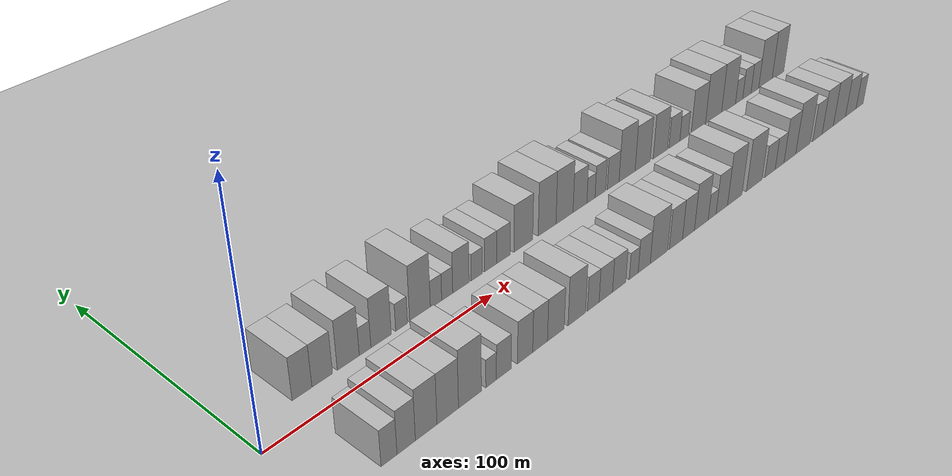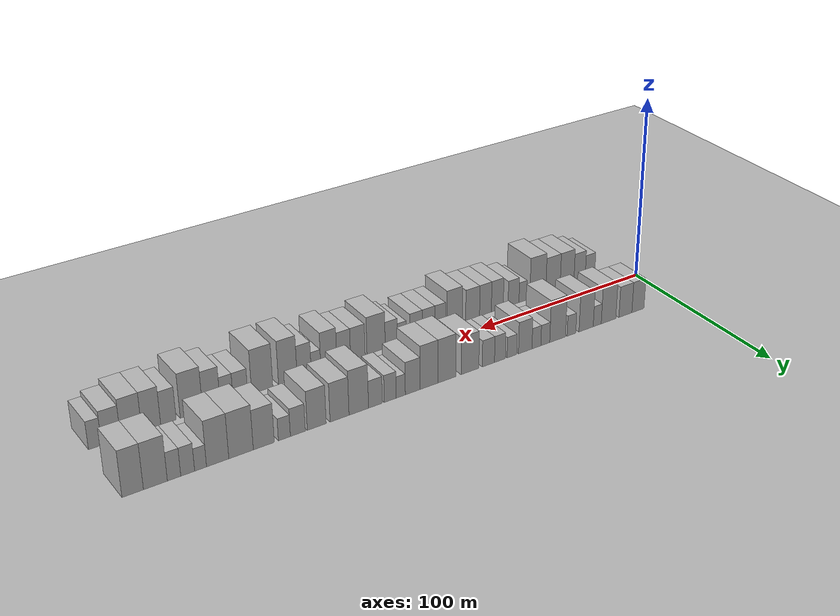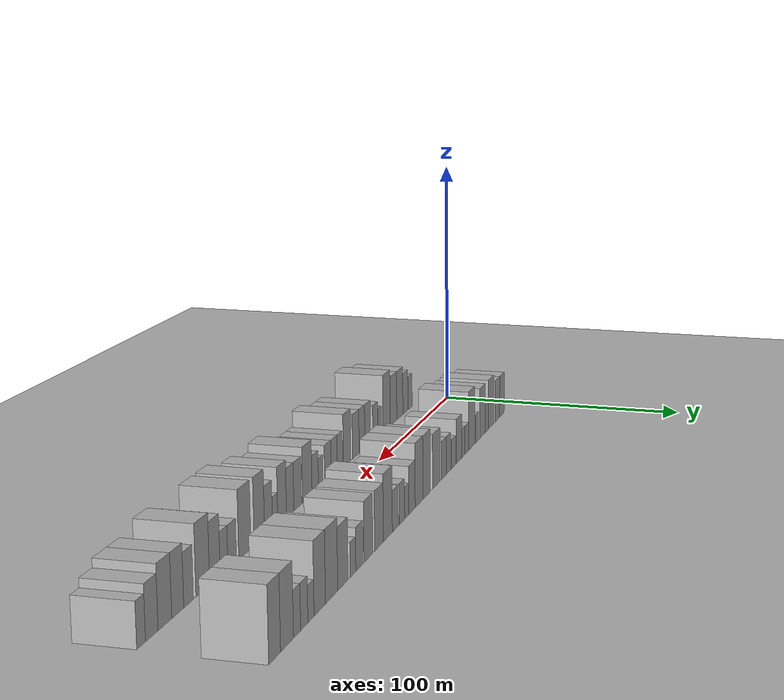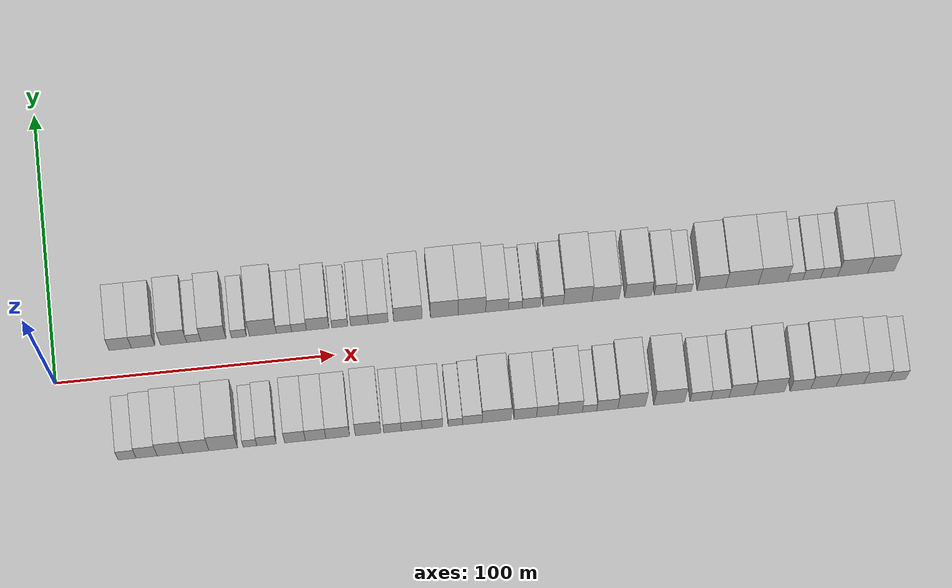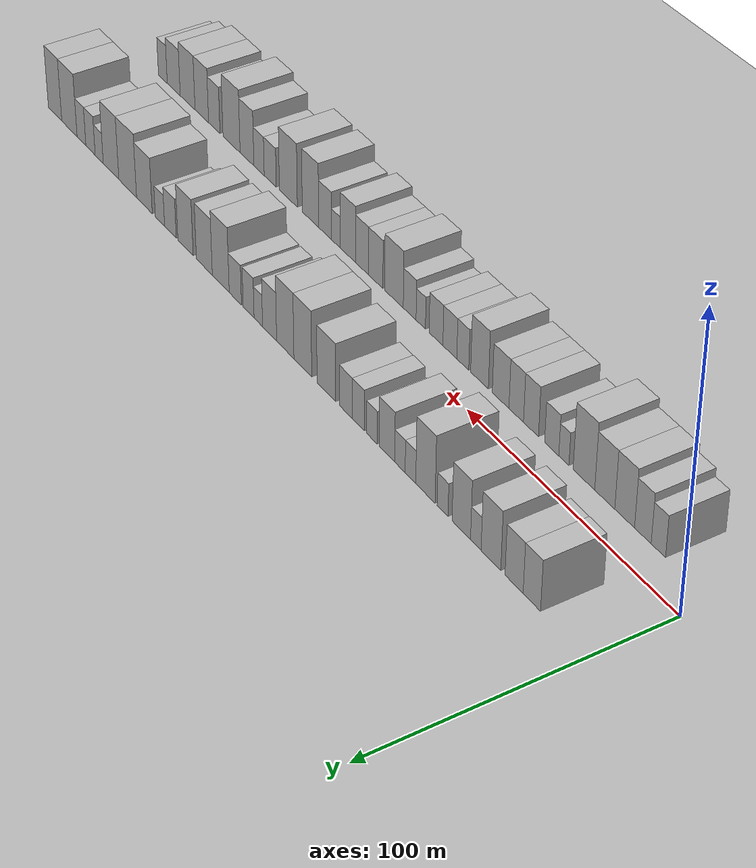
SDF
<?xml version="1.0" encoding="utf-8"?>

<sdf version="1.6">

   <world name="default">

      <gui fullscreen="0">

         <camera name="user_camera">

            <pose>-15 0 4.57585 0 0 0</pose>

            <view_controller>orbit</view_controller>

         </camera>

      </gui>

      <scene>

         <sky>

           <clouds>

             <speed>12</speed>

           </clouds>

         </sky>

         <ambient>0.4 0.4 0.4 1</ambient>

         <background>0.7 0.7 0.7 1</background>

         <shadows>1</shadows>

      </scene>

      <gravity>0 0 -9.8066</gravity>

      <magnetic_field>6e-06 2.3e-05 -4.2e-05</magnetic_field>

      <physics default="0" name="default_physics" type="ode">

         <ode>

            <solver>

               <type>quick</type>

               <iters>10</iters>

               <sor>1.0</sor>

               <use_dynamic_moi_rescaling>0</use_dynamic_moi_rescaling>

            </solver>

            <constraints>

               <cfm>0</cfm>

               <erp>0.2</erp>

               <contact_max_correcting_vel>100</contact_max_correcting_vel>

               <contact_surface_layer>0.001</contact_surface_layer>

            </constraints>

         </ode>

         <max_step_size>0.004</max_step_size>

         <real_time_factor>1</real_time_factor>

         <real_time_update_rate>250</real_time_update_rate>

      </physics>

      <light name="sun" type="directional">

         <cast_shadows>1</cast_shadows>

         <pose>0 0 10 0 0 0</pose>

         <diffuse>0.8 0.8 0.8 1</diffuse>

         <specular>0.2 0.2 0.2 1</specular>

         <attenuation>

            <range>1000</range>

            <constant>0.9</constant>

            <linear>0.01</linear>

            <quadratic>0.001</quadratic>

         </attenuation>

         <direction>-0.5 0.1 -0.9</direction>

      </light>

      <include>

         <name>ground_plane_1</name>

         <uri>model://HANNAS_ground_plane</uri>

         <pose>0 0 0  0 0 0</pose>

      </include>

      <include>

         <name>ground_plane_2</name>

         <uri>model://HANNAS_ground_plane</uri>

         <pose>100 0 0  0 0 0</pose>

      </include>

      <model name="building_1">

         <static>1</static>

         <pose frame="">23.9908 20.0000 0 0.000000 0.000000 1.570796</pose>

         <link name="link">

            <pose frame="">0 0 9.00 0 0 0</pose>

            <collision name="collision">

               <geometry>

                  <box>

                     <size>20.0000 7.9815 18.0000</size>

                  </box>

               </geometry>

               <max_contacts>10</max_contacts>

               <surface>

                  <contact>

                     <ode/>

                  </contact>

                  <bounce/>

                  <friction>

                     <torsional>

                        <ode/>

                     </torsional>

                     <ode/>

                  </friction>

               </surface>

            </collision>

            <visual name="visual">

               <cast_shadows>0</cast_shadows>

               <geometry>

                  <box>

                     <size>20.0000 7.9815 18.0000</size>

                  </box>

               </geometry>

               <material>

                  <script>

                     <uri>model://HANNAS_wall/materials/scripts</uri>

                     <uri>model://HANNAS_wall/materials/textures</uri>

                     <name>vrc/HANNAS_wall</name>

                  </script>

               </material>

            </visual>

            <self_collide>0</self_collide>

            <enable_wind>0</enable_wind>

            <kinematic>0</kinematic>

         </link>

      </model>

      <model name="building_2">

         <static>1</static>

         <pose frame="">32.2059 20.0000 0 0.000000 0.000000 1.570796</pose>

         <link name="link">

            <pose frame="">0 0 9.00 0 0 0</pose>

            <collision name="collision">

               <geometry>

                  <box>

                     <size>20.0000 8.4488 18.0000</size>

                  </box>

               </geometry>

               <max_contacts>10</max_contacts>

               <surface>

                  <contact>

                     <ode/>

                  </contact>

                  <bounce/>

                  <friction>

                     <torsional>

                        <ode/>

                     </torsional>

                     <ode/>

                  </friction>

               </surface>

            </collision>

            <visual name="visual">

               <cast_shadows>0</cast_shadows>

               <geometry>

                  <box>

                     <size>20.0000 8.4488 18.0000</size>

                  </box>

               </geometry>

               <material>

                  <script>

                     <uri>model://HANNAS_wall/materials/scripts</uri>

                     <uri>model://HANNAS_wall/materials/textures</uri>

                     <name>vrc/HANNAS_wall</name>

                  </script>

               </material>

            </visual>

            <self_collide>0</self_collide>

            <enable_wind>0</enable_wind>

            <kinematic>0</kinematic>

         </link>

      </model>

      <model name="building_3">

         <static>1</static>

         <pose frame="">43.1120 20.0000 0 0.000000 0.000000 1.570796</pose>

         <link name="link">

            <pose frame="">0 0 10.50 0 0 0</pose>

            <collision name="collision">

               <geometry>

                  <box>

                     <size>20.0000 9.3635 21.0000</size>

                  </box>

               </geometry>

               <max_contacts>10</max_contacts>

               <surface>

                  <contact>

                     <ode/>

                  </contact>

                  <bounce/>

                  <friction>

                     <torsional>

                        <ode/>

                     </torsional>

                     <ode/>

                  </friction>

               </surface>

            </collision>

            <visual name="visual">

               <cast_shadows>0</cast_shadows>

               <geometry>

                  <box>

                     <size>20.0000 9.3635 21.0000</size>

                  </box>

               </geometry>

               <material>

                  <script>

                     <uri>model://HANNAS_wall/materials/scripts</uri>

                     <uri>model://HANNAS_wall/materials/textures</uri>

                     <name>vrc/HANNAS_wall</name>

                  </script>

               </material>

            </visual>

            <self_collide>0</self_collide>

            <enable_wind>0</enable_wind>

            <kinematic>0</kinematic>

         </link>

      </model>

      <model name="building_4">

         <static>1</static>

         <pose frame="">50.3294 20.0000 0 0.000000 0.000000 1.570796</pose>

         <link name="link">

            <pose frame="">0 0 6.00 0 0 0</pose>

            <collision name="collision">

               <geometry>

                  <box>

                     <size>20.0000 5.0712 12.0000</size>

                  </box>

               </geometry>

               <max_contacts>10</max_contacts>

               <surface>

                  <contact>

                     <ode/>

                  </contact>

                  <bounce/>

                  <friction>

                     <torsional>

                        <ode/>

                     </torsional>

                     <ode/>

                  </friction>

               </surface>

            </collision>

            <visual name="visual">

               <cast_shadows>0</cast_shadows>

               <geometry>

                  <box>

                     <size>20.0000 5.0712 12.0000</size>

                  </box>

               </geometry>

               <material>

                  <script>

                     <uri>model://HANNAS_wall/materials/scripts</uri>

                     <uri>model://HANNAS_wall/materials/textures</uri>

                     <name>vrc/HANNAS_wall</name>

                  </script>

               </material>

            </visual>

            <self_collide>0</self_collide>

            <enable_wind>0</enable_wind>

            <kinematic>0</kinematic>

         </link>

      </model>

      <model name="building_5">

         <static>1</static>

         <pose frame="">57.3656 20.0000 0 0.000000 0.000000 1.570796</pose>

         <link name="link">

            <pose frame="">0 0 10.50 0 0 0</pose>

            <collision name="collision">

               <geometry>

                  <box>

                     <size>20.0000 9.0012 21.0000</size>

                  </box>

               </geometry>

               <max_contacts>10</max_contacts>

               <surface>

                  <contact>

                     <ode/>

                  </contact>

                  <bounce/>

                  <friction>

                     <torsional>

                        <ode/>

                     </torsional>

                     <ode/>

                  </friction>

               </surface>

            </collision>

            <visual name="visual">

               <cast_shadows>0</cast_shadows>

               <geometry>

                  <box>

                     <size>20.0000 9.0012 21.0000</size>

                  </box>

               </geometry>

               <material>

                  <script>

                     <uri>model://HANNAS_wall/materials/scripts</uri>

                     <uri>model://HANNAS_wall/materials/textures</uri>

                     <name>vrc/HANNAS_wall</name>

                  </script>

               </material>

            </visual>

            <self_collide>0</self_collide>

            <enable_wind>0</enable_wind>

            <kinematic>0</kinematic>

         </link>

      </model>

      <model name="building_6">

         <static>1</static>

         <pose frame="">66.5707 20.0000 0 0.000000 0.000000 1.570796</pose>

         <link name="link">

            <pose frame="">0 0 6.00 0 0 0</pose>

            <collision name="collision">

               <geometry>

                  <box>

                     <size>20.0000 5.4089 12.0000</size>

                  </box>

               </geometry>

               <max_contacts>10</max_contacts>

               <surface>

                  <contact>

                     <ode/>

                  </contact>

                  <bounce/>

                  <friction>

                     <torsional>

                        <ode/>

                     </torsional>

                     <ode/>

                  </friction>

               </surface>

            </collision>

            <visual name="visual">

               <cast_shadows>0</cast_shadows>

               <geometry>

                  <box>

                     <size>20.0000 5.4089 12.0000</size>

                  </box>

               </geometry>

               <material>

                  <script>

                     <uri>model://HANNAS_wall/materials/scripts</uri>

                     <uri>model://HANNAS_wall/materials/textures</uri>

                     <name>vrc/HANNAS_wall</name>

                  </script>

               </material>

            </visual>

            <self_collide>0</self_collide>

            <enable_wind>0</enable_wind>

            <kinematic>0</kinematic>

         </link>

      </model>

      <model name="building_7">

         <static>1</static>

         <pose frame="">75.1345 20.0000 0 0.000000 0.000000 1.570796</pose>

         <link name="link">

            <pose frame="">0 0 12.00 0 0 0</pose>

            <collision name="collision">

               <geometry>

                  <box>

                     <size>20.0000 9.7187 24.0000</size>

                  </box>

               </geometry>

               <max_contacts>10</max_contacts>

               <surface>

                  <contact>

                     <ode/>

                  </contact>

                  <bounce/>

                  <friction>

                     <torsional>

                        <ode/>

                     </torsional>

                     <ode/>

                  </friction>

               </surface>

            </collision>

            <visual name="visual">

               <cast_shadows>0</cast_shadows>

               <geometry>

                  <box>

                     <size>20.0000 9.7187 24.0000</size>

                  </box>

               </geometry>

               <material>

                  <script>

                     <uri>model://HANNAS_wall/materials/scripts</uri>

                     <uri>model://HANNAS_wall/materials/textures</uri>

                     <name>vrc/HANNAS_wall</name>

                  </script>

               </material>

            </visual>

            <self_collide>0</self_collide>

            <enable_wind>0</enable_wind>

            <kinematic>0</kinematic>

         </link>

      </model>

      <model name="building_8">

         <static>1</static>

         <pose frame="">82.7058 20.0000 0 0.000000 0.000000 1.570796</pose>

         <link name="link">

            <pose frame="">0 0 6.00 0 0 0</pose>

            <collision name="collision">

               <geometry>

                  <box>

                     <size>20.0000 5.4239 12.0000</size>

                  </box>

               </geometry>

               <max_contacts>10</max_contacts>

               <surface>

                  <contact>

                     <ode/>

                  </contact>

                  <bounce/>

                  <friction>

                     <torsional>

                        <ode/>

                     </torsional>

                     <ode/>

                  </friction>

               </surface>

            </collision>

            <visual name="visual">

               <cast_shadows>0</cast_shadows>

               <geometry>

                  <box>

                     <size>20.0000 5.4239 12.0000</size>

                  </box>

               </geometry>

               <material>

                  <script>

                     <uri>model://HANNAS_wall/materials/scripts</uri>

                     <uri>model://HANNAS_wall/materials/textures</uri>

                     <name>vrc/HANNAS_wall</name>

                  </script>

               </material>

            </visual>

            <self_collide>0</self_collide>

            <enable_wind>0</enable_wind>

            <kinematic>0</kinematic>

         </link>

      </model>

      <model name="building_9">

         <static>1</static>

         <pose frame="">88.1032 20.0000 0 0.000000 0.000000 1.570796</pose>

         <link name="link">

            <pose frame="">0 0 6.00 0 0 0</pose>

            <collision name="collision">

               <geometry>

                  <box>

                     <size>20.0000 5.3708 12.0000</size>

                  </box>

               </geometry>

               <max_contacts>10</max_contacts>

               <surface>

                  <contact>

                     <ode/>

                  </contact>

                  <bounce/>

                  <friction>

                     <torsional>

                        <ode/>

                     </torsional>

                     <ode/>

                  </friction>

               </surface>

            </collision>

            <visual name="visual">

               <cast_shadows>0</cast_shadows>

               <geometry>

                  <box>

                     <size>20.0000 5.3708 12.0000</size>

                  </box>

               </geometry>

               <material>

                  <script>

                     <uri>model://HANNAS_wall/materials/scripts</uri>

                     <uri>model://HANNAS_wall/materials/textures</uri>

                     <name>vrc/HANNAS_wall</name>

                  </script>

               </material>

            </visual>

            <self_collide>0</self_collide>

            <enable_wind>0</enable_wind>

            <kinematic>0</kinematic>

         </link>

      </model>

      <model name="building_10">

         <static>1</static>

         <pose frame="">94.8376 20.0000 0 0.000000 0.000000 1.570796</pose>

         <link name="link">

            <pose frame="">0 0 9.00 0 0 0</pose>

            <collision name="collision">

               <geometry>

                  <box>

                     <size>20.0000 8.0981 18.0000</size>

                  </box>

               </geometry>

               <max_contacts>10</max_contacts>

               <surface>

                  <contact>

                     <ode/>

                  </contact>

                  <bounce/>

                  <friction>

                     <torsional>

                        <ode/>

                     </torsional>

                     <ode/>

                  </friction>

               </surface>

            </collision>

            <visual name="visual">

               <cast_shadows>0</cast_shadows>

               <geometry>

                  <box>

                     <size>20.0000 8.0981 18.0000</size>

                  </box>

               </geometry>

               <material>

                  <script>

                     <uri>model://HANNAS_wall/materials/scripts</uri>

                     <uri>model://HANNAS_wall/materials/textures</uri>

                     <name>vrc/HANNAS_wall</name>

                  </script>

               </material>

            </visual>

            <self_collide>0</self_collide>

            <enable_wind>0</enable_wind>

            <kinematic>0</kinematic>

         </link>

      </model>

      <model name="building_11">

         <static>1</static>

         <pose frame="">102.7686 20.0000 0 0.000000 0.000000 1.570796</pose>

         <link name="link">

            <pose frame="">0 0 6.00 0 0 0</pose>

            <collision name="collision">

               <geometry>

                  <box>

                     <size>20.0000 5.7640 12.0000</size>

                  </box>

               </geometry>

               <max_contacts>10</max_contacts>

               <surface>

                  <contact>

                     <ode/>

                  </contact>

                  <bounce/>

                  <friction>

                     <torsional>

                        <ode/>

                     </torsional>

                     <ode/>

                  </friction>

               </surface>

            </collision>

            <visual name="visual">

               <cast_shadows>0</cast_shadows>

               <geometry>

                  <box>

                     <size>20.0000 5.7640 12.0000</size>

                  </box>

               </geometry>

               <material>

                  <script>

                     <uri>model://HANNAS_wall/materials/scripts</uri>

                     <uri>model://HANNAS_wall/materials/textures</uri>

                     <name>vrc/HANNAS_wall</name>

                  </script>

               </material>

            </visual>

            <self_collide>0</self_collide>

            <enable_wind>0</enable_wind>

            <kinematic>0</kinematic>

         </link>

      </model>

      <model name="building_12">

         <static>1</static>

         <pose frame="">109.8444 20.0000 0 0.000000 0.000000 1.570796</pose>

         <link name="link">

            <pose frame="">0 0 7.50 0 0 0</pose>

            <collision name="collision">

               <geometry>

                  <box>

                     <size>20.0000 6.3876 15.0000</size>

                  </box>

               </geometry>

               <max_contacts>10</max_contacts>

               <surface>

                  <contact>

                     <ode/>

                  </contact>

                  <bounce/>

                  <friction>

                     <torsional>

                        <ode/>

                     </torsional>

                     <ode/>

                  </friction>

               </surface>

            </collision>

            <visual name="visual">

               <cast_shadows>0</cast_shadows>

               <geometry>

                  <box>

                     <size>20.0000 6.3876 15.0000</size>

                  </box>

               </geometry>

               <material>

                  <script>

                     <uri>model://HANNAS_wall/materials/scripts</uri>

                     <uri>model://HANNAS_wall/materials/textures</uri>

                     <name>vrc/HANNAS_wall</name>

                  </script>

               </material>

            </visual>

            <self_collide>0</self_collide>

            <enable_wind>0</enable_wind>

            <kinematic>0</kinematic>

         </link>

      </model>

      <model name="building_13">

         <static>1</static>

         <pose frame="">116.5820 20.0000 0 0.000000 0.000000 1.570796</pose>

         <link name="link">

            <pose frame="">0 0 7.50 0 0 0</pose>

            <collision name="collision">

               <geometry>

                  <box>

                     <size>20.0000 7.0874 15.0000</size>

                  </box>

               </geometry>

               <max_contacts>10</max_contacts>

               <surface>

                  <contact>

                     <ode/>

                  </contact>

                  <bounce/>

                  <friction>

                     <torsional>

                        <ode/>

                     </torsional>

                     <ode/>

                  </friction>

               </surface>

            </collision>

            <visual name="visual">

               <cast_shadows>0</cast_shadows>

               <geometry>

                  <box>

                     <size>20.0000 7.0874 15.0000</size>

                  </box>

               </geometry>

               <material>

                  <script>

                     <uri>model://HANNAS_wall/materials/scripts</uri>

                     <uri>model://HANNAS_wall/materials/textures</uri>

                     <name>vrc/HANNAS_wall</name>

                  </script>

               </material>

            </visual>

            <self_collide>0</self_collide>

            <enable_wind>0</enable_wind>

            <kinematic>0</kinematic>

         </link>

      </model>

      <model name="building_14">

         <static>1</static>

         <pose frame="">127.2377 20.0000 0 0.000000 0.000000 1.570796</pose>

         <link name="link">

            <pose frame="">0 0 10.50 0 0 0</pose>

            <collision name="collision">

               <geometry>

                  <box>

                     <size>20.0000 10.2242 21.0000</size>

                  </box>

               </geometry>

               <max_contacts>10</max_contacts>

               <surface>

                  <contact>

                     <ode/>

                  </contact>

                  <bounce/>

                  <friction>

                     <torsional>

                        <ode/>

                     </torsional>

                     <ode/>

                  </friction>

               </surface>

            </collision>

            <visual name="visual">

               <cast_shadows>0</cast_shadows>

               <geometry>

                  <box>

                     <size>20.0000 10.2242 21.0000</size>

                  </box>

               </geometry>

               <material>

                  <script>

                     <uri>model://HANNAS_wall/materials/scripts</uri>

                     <uri>model://HANNAS_wall/materials/textures</uri>

                     <name>vrc/HANNAS_wall</name>

                  </script>

               </material>

            </visual>

            <self_collide>0</self_collide>

            <enable_wind>0</enable_wind>

            <kinematic>0</kinematic>

         </link>

      </model>

      <model name="building_15">

         <static>1</static>

         <pose frame="">140.3518 20.0000 0 0.000000 0.000000 1.570796</pose>

         <link name="link">

            <pose frame="">0 0 12.00 0 0 0</pose>

            <collision name="collision">

               <geometry>

                  <box>

                     <size>20.0000 10.0040 24.0000</size>

                  </box>

               </geometry>

               <max_contacts>10</max_contacts>

               <surface>

                  <contact>

                     <ode/>

                  </contact>

                  <bounce/>

                  <friction>

                     <torsional>

                        <ode/>

                     </torsional>

                     <ode/>

                  </friction>

               </surface>

            </collision>

            <visual name="visual">

               <cast_shadows>0</cast_shadows>

               <geometry>

                  <box>

                     <size>20.0000 10.0040 24.0000</size>

                  </box>

               </geometry>

               <material>

                  <script>

                     <uri>model://HANNAS_wall/materials/scripts</uri>

                     <uri>model://HANNAS_wall/materials/textures</uri>

                     <name>vrc/HANNAS_wall</name>

                  </script>

               </material>

            </visual>

            <self_collide>0</self_collide>

            <enable_wind>0</enable_wind>

            <kinematic>0</kinematic>

         </link>

      </model>

      <model name="building_16">

         <static>1</static>

         <pose frame="">150.2946 20.0000 0 0.000000 0.000000 1.570796</pose>

         <link name="link">

            <pose frame="">0 0 12.00 0 0 0</pose>

            <collision name="collision">

               <geometry>

                  <box>

                     <size>20.0000 9.8817 24.0000</size>

                  </box>

               </geometry>

               <max_contacts>10</max_contacts>

               <surface>

                  <contact>

                     <ode/>

                  </contact>

                  <bounce/>

                  <friction>

                     <torsional>

                        <ode/>

                     </torsional>

                     <ode/>

                  </friction>

               </surface>

            </collision>

            <visual name="visual">

               <cast_shadows>0</cast_shadows>

               <geometry>

                  <box>

                     <size>20.0000 9.8817 24.0000</size>

                  </box>

               </geometry>

               <material>

                  <script>

                     <uri>model://HANNAS_wall/materials/scripts</uri>

                     <uri>model://HANNAS_wall/materials/textures</uri>

                     <name>vrc/HANNAS_wall</name>

                  </script>

               </material>

            </visual>

            <self_collide>0</self_collide>

            <enable_wind>0</enable_wind>

            <kinematic>0</kinematic>

         </link>

      </model>

      <model name="building_17">

         <static>1</static>

         <pose frame="">159.3237 20.0000 0 0.000000 0.000000 1.570796</pose>

         <link name="link">

            <pose frame="">0 0 9.00 0 0 0</pose>

            <collision name="collision">

               <geometry>

                  <box>

                     <size>20.0000 8.1764 18.0000</size>

                  </box>

               </geometry>

               <max_contacts>10</max_contacts>

               <surface>

                  <contact>

                     <ode/>

                  </contact>

                  <bounce/>

                  <friction>

                     <torsional>

                        <ode/>

                     </torsional>

                     <ode/>

                  </friction>

               </surface>

            </collision>

            <visual name="visual">

               <cast_shadows>0</cast_shadows>

               <geometry>

                  <box>

                     <size>20.0000 8.1764 18.0000</size>

                  </box>

               </geometry>

               <material>

                  <script>

                     <uri>model://HANNAS_wall/materials/scripts</uri>

                     <uri>model://HANNAS_wall/materials/textures</uri>

                     <name>vrc/HANNAS_wall</name>

                  </script>

               </material>

            </visual>

            <self_collide>0</self_collide>

            <enable_wind>0</enable_wind>

            <kinematic>0</kinematic>

         </link>

      </model>

      <model name="building_18">

         <static>1</static>

         <pose frame="">165.8892 20.0000 0 0.000000 0.000000 1.570796</pose>

         <link name="link">

            <pose frame="">0 0 6.00 0 0 0</pose>

            <collision name="collision">

               <geometry>

                  <box>

                     <size>20.0000 4.9546 12.0000</size>

                  </box>

               </geometry>

               <max_contacts>10</max_contacts>

               <surface>

                  <contact>

                     <ode/>

                  </contact>

                  <bounce/>

                  <friction>

                     <torsional>

                        <ode/>

                     </torsional>

                     <ode/>

                  </friction>

               </surface>

            </collision>

            <visual name="visual">

               <cast_shadows>0</cast_shadows>

               <geometry>

                  <box>

                     <size>20.0000 4.9546 12.0000</size>

                  </box>

               </geometry>

               <material>

                  <script>

                     <uri>model://HANNAS_wall/materials/scripts</uri>

                     <uri>model://HANNAS_wall/materials/textures</uri>

                     <name>vrc/HANNAS_wall</name>

                  </script>

               </material>

            </visual>

            <self_collide>0</self_collide>

            <enable_wind>0</enable_wind>

            <kinematic>0</kinematic>

         </link>

      </model>

      <model name="building_19">

         <static>1</static>

         <pose frame="">171.5991 20.0000 0 0.000000 0.000000 1.570796</pose>

         <link name="link">

            <pose frame="">0 0 7.50 0 0 0</pose>

            <collision name="collision">

               <geometry>

                  <box>

                     <size>20.0000 6.4652 15.0000</size>

                  </box>

               </geometry>

               <max_contacts>10</max_contacts>

               <surface>

                  <contact>

                     <ode/>

                  </contact>

                  <bounce/>

                  <friction>

                     <torsional>

                        <ode/>

                     </torsional>

                     <ode/>

                  </friction>

               </surface>

            </collision>

            <visual name="visual">

               <cast_shadows>0</cast_shadows>

               <geometry>

                  <box>

                     <size>20.0000 6.4652 15.0000</size>

                  </box>

               </geometry>

               <material>

                  <script>

                     <uri>model://HANNAS_wall/materials/scripts</uri>

                     <uri>model://HANNAS_wall/materials/textures</uri>

                     <name>vrc/HANNAS_wall</name>

                  </script>

               </material>

            </visual>

            <self_collide>0</self_collide>

            <enable_wind>0</enable_wind>

            <kinematic>0</kinematic>

         </link>

      </model>

      <model name="building_20">

         <static>1</static>

         <pose frame="">179.5096 20.0000 0 0.000000 0.000000 1.570796</pose>

         <link name="link">

            <pose frame="">0 0 7.50 0 0 0</pose>

            <collision name="collision">

               <geometry>

                  <box>

                     <size>20.0000 7.3557 15.0000</size>

                  </box>

               </geometry>

               <max_contacts>10</max_contacts>

               <surface>

                  <contact>

                     <ode/>

                  </contact>

                  <bounce/>

                  <friction>

                     <torsional>

                        <ode/>

                     </torsional>

                     <ode/>

                  </friction>

               </surface>

            </collision>

            <visual name="visual">

               <cast_shadows>0</cast_shadows>

               <geometry>

                  <box>

                     <size>20.0000 7.3557 15.0000</size>

                  </box>

               </geometry>

               <material>

                  <script>

                     <uri>model://HANNAS_wall/materials/scripts</uri>

                     <uri>model://HANNAS_wall/materials/textures</uri>

                     <name>vrc/HANNAS_wall</name>

                  </script>

               </material>

            </visual>

            <self_collide>0</self_collide>

            <enable_wind>0</enable_wind>

            <kinematic>0</kinematic>

         </link>

      </model>

      <model name="building_21">

         <static>1</static>

         <pose frame="">188.3211 20.0000 0 0.000000 0.000000 1.570796</pose>

         <link name="link">

            <pose frame="">0 0 12.00 0 0 0</pose>

            <collision name="collision">

               <geometry>

                  <box>

                     <size>20.0000 10.2673 24.0000</size>

                  </box>

               </geometry>

               <max_contacts>10</max_contacts>

               <surface>

                  <contact>

                     <ode/>

                  </contact>

                  <bounce/>

                  <friction>

                     <torsional>

                        <ode/>

                     </torsional>

                     <ode/>

                  </friction>

               </surface>

            </collision>

            <visual name="visual">

               <cast_shadows>0</cast_shadows>

               <geometry>

                  <box>

                     <size>20.0000 10.2673 24.0000</size>

                  </box>

               </geometry>

               <material>

                  <script>

                     <uri>model://HANNAS_wall/materials/scripts</uri>

                     <uri>model://HANNAS_wall/materials/textures</uri>

                     <name>vrc/HANNAS_wall</name>

                  </script>

               </material>

            </visual>

            <self_collide>0</self_collide>

            <enable_wind>0</enable_wind>

            <kinematic>0</kinematic>

         </link>

      </model>

      <model name="building_22">

         <static>1</static>

         <pose frame="">198.3743 20.0000 0 0.000000 0.000000 1.570796</pose>

         <link name="link">

            <pose frame="">0 0 10.50 0 0 0</pose>

            <collision name="collision">

               <geometry>

                  <box>

                     <size>20.0000 9.8392 21.0000</size>

                  </box>

               </geometry>

               <max_contacts>10</max_contacts>

               <surface>

                  <contact>

                     <ode/>

                  </contact>

                  <bounce/>

                  <friction>

                     <torsional>

                        <ode/>

                     </torsional>

                     <ode/>

                  </friction>

               </surface>

            </collision>

            <visual name="visual">

               <cast_shadows>0</cast_shadows>

               <geometry>

                  <box>

                     <size>20.0000 9.8392 21.0000</size>

                  </box>

               </geometry>

               <material>

                  <script>

                     <uri>model://HANNAS_wall/materials/scripts</uri>

                     <uri>model://HANNAS_wall/materials/textures</uri>

                     <name>vrc/HANNAS_wall</name>

                  </script>

               </material>

            </visual>

            <self_collide>0</self_collide>

            <enable_wind>0</enable_wind>

            <kinematic>0</kinematic>

         </link>

      </model>

      <model name="building_23">

         <static>1</static>

         <pose frame="">210.1101 20.0000 0 0.000000 0.000000 1.570796</pose>

         <link name="link">

            <pose frame="">0 0 10.50 0 0 0</pose>

            <collision name="collision">

               <geometry>

                  <box>

                     <size>20.0000 9.6324 21.0000</size>

                  </box>

               </geometry>

               <max_contacts>10</max_contacts>

               <surface>

                  <contact>

                     <ode/>

                  </contact>

                  <bounce/>

                  <friction>

                     <torsional>

                        <ode/>

                     </torsional>

                     <ode/>

                  </friction>

               </surface>

            </collision>

            <visual name="visual">

               <cast_shadows>0</cast_shadows>

               <geometry>

                  <box>

                     <size>20.0000 9.6324 21.0000</size>

                  </box>

               </geometry>

               <material>

                  <script>

                     <uri>model://HANNAS_wall/materials/scripts</uri>

                     <uri>model://HANNAS_wall/materials/textures</uri>

                     <name>vrc/HANNAS_wall</name>

                  </script>

               </material>

            </visual>

            <self_collide>0</self_collide>

            <enable_wind>0</enable_wind>

            <kinematic>0</kinematic>

         </link>

      </model>

      <model name="building_24">

         <static>1</static>

         <pose frame="">219.6738 20.0000 0 0.000000 0.000000 1.570796</pose>

         <link name="link">

            <pose frame="">0 0 7.50 0 0 0</pose>

            <collision name="collision">

               <geometry>

                  <box>

                     <size>20.0000 7.4949 15.0000</size>

                  </box>

               </geometry>

               <max_contacts>10</max_contacts>

               <surface>

                  <contact>

                     <ode/>

                  </contact>

                  <bounce/>

                  <friction>

                     <torsional>

                        <ode/>

                     </torsional>

                     <ode/>

                  </friction>

               </surface>

            </collision>

            <visual name="visual">

               <cast_shadows>0</cast_shadows>

               <geometry>

                  <box>

                     <size>20.0000 7.4949 15.0000</size>

                  </box>

               </geometry>

               <material>

                  <script>

                     <uri>model://HANNAS_wall/materials/scripts</uri>

                     <uri>model://HANNAS_wall/materials/textures</uri>

                     <name>vrc/HANNAS_wall</name>

                  </script>

               </material>

            </visual>

            <self_collide>0</self_collide>

            <enable_wind>0</enable_wind>

            <kinematic>0</kinematic>

         </link>

      </model>

      <model name="building_25">

         <static>1</static>

         <pose frame="">226.4071 20.0000 0 0.000000 0.000000 1.570796</pose>

         <link name="link">

            <pose frame="">0 0 6.00 0 0 0</pose>

            <collision name="collision">

               <geometry>

                  <box>

                     <size>20.0000 5.9717 12.0000</size>

                  </box>

               </geometry>

               <max_contacts>10</max_contacts>

               <surface>

                  <contact>

                     <ode/>

                  </contact>

                  <bounce/>

                  <friction>

                     <torsional>

                        <ode/>

                     </torsional>

                     <ode/>

                  </friction>

               </surface>

            </collision>

            <visual name="visual">

               <cast_shadows>0</cast_shadows>

               <geometry>

                  <box>

                     <size>20.0000 5.9717 12.0000</size>

                  </box>

               </geometry>

               <material>

                  <script>

                     <uri>model://HANNAS_wall/materials/scripts</uri>

                     <uri>model://HANNAS_wall/materials/textures</uri>

                     <name>vrc/HANNAS_wall</name>

                  </script>

               </material>

            </visual>

            <self_collide>0</self_collide>

            <enable_wind>0</enable_wind>

            <kinematic>0</kinematic>

         </link>

      </model>

      <model name="building_26">

         <static>1</static>

         <pose frame="">236.5378 20.0000 0 0.000000 0.000000 1.570796</pose>

         <link name="link">

            <pose frame="">0 0 10.50 0 0 0</pose>

            <collision name="collision">

               <geometry>

                  <box>

                     <size>20.0000 10.2896 21.0000</size>

                  </box>

               </geometry>

               <max_contacts>10</max_contacts>

               <surface>

                  <contact>

                     <ode/>

                  </contact>

                  <bounce/>

                  <friction>

                     <torsional>

                        <ode/>

                     </torsional>

                     <ode/>

                  </friction>

               </surface>

            </collision>

            <visual name="visual">

               <cast_shadows>0</cast_shadows>

               <geometry>

                  <box>

                     <size>20.0000 10.2896 21.0000</size>

                  </box>

               </geometry>

               <material>

                  <script>

                     <uri>model://HANNAS_wall/materials/scripts</uri>

                     <uri>model://HANNAS_wall/materials/textures</uri>

                     <name>vrc/HANNAS_wall</name>

                  </script>

               </material>

            </visual>

            <self_collide>0</self_collide>

            <enable_wind>0</enable_wind>

            <kinematic>0</kinematic>

         </link>

      </model>

      <model name="building_27">

         <static>1</static>

         <pose frame="">247.5895 20.0000 0 0.000000 0.000000 1.570796</pose>

         <link name="link">

            <pose frame="">0 0 12.00 0 0 0</pose>

            <collision name="collision">

               <geometry>

                  <box>

                     <size>20.0000 11.8139 24.0000</size>

                  </box>

               </geometry>

               <max_contacts>10</max_contacts>

               <surface>

                  <contact>

                     <ode/>

                  </contact>

                  <bounce/>

                  <friction>

                     <torsional>

                        <ode/>

                     </torsional>

                     <ode/>

                  </friction>

               </surface>

            </collision>

            <visual name="visual">

               <cast_shadows>0</cast_shadows>

               <geometry>

                  <box>

                     <size>20.0000 11.8139 24.0000</size>

                  </box>

               </geometry>

               <material>

                  <script>

                     <uri>model://HANNAS_wall/materials/scripts</uri>

                     <uri>model://HANNAS_wall/materials/textures</uri>

                     <name>vrc/HANNAS_wall</name>

                  </script>

               </material>

            </visual>

            <self_collide>0</self_collide>

            <enable_wind>0</enable_wind>

            <kinematic>0</kinematic>

         </link>

      </model>

      <model name="building_28">

         <static>1</static>

         <pose frame="">258.7789 20.0000 0 0.000000 0.000000 1.570796</pose>

         <link name="link">

            <pose frame="">0 0 12.00 0 0 0</pose>

            <collision name="collision">

               <geometry>

                  <box>

                     <size>20.0000 10.5648 24.0000</size>

                  </box>

               </geometry>

               <max_contacts>10</max_contacts>

               <surface>

                  <contact>

                     <ode/>

                  </contact>

                  <bounce/>

                  <friction>

                     <torsional>

                        <ode/>

                     </torsional>

                     <ode/>

                  </friction>

               </surface>

            </collision>

            <visual name="visual">

               <cast_shadows>0</cast_shadows>

               <geometry>

                  <box>

                     <size>20.0000 10.5648 24.0000</size>

                  </box>

               </geometry>

               <material>

                  <script>

                     <uri>model://HANNAS_wall/materials/scripts</uri>

                     <uri>model://HANNAS_wall/materials/textures</uri>

                     <name>vrc/HANNAS_wall</name>

                  </script>

               </material>

            </visual>

            <self_collide>0</self_collide>

            <enable_wind>0</enable_wind>

            <kinematic>0</kinematic>

         </link>

      </model>

      <model name="building_29">

         <static>1</static>

         <pose frame="">266.8416 20.0000 0 0.000000 0.000000 1.570796</pose>

         <link name="link">

            <pose frame="">0 0 6.00 0 0 0</pose>

            <collision name="collision">

               <geometry>

                  <box>

                     <size>20.0000 5.5606 12.0000</size>

                  </box>

               </geometry>

               <max_contacts>10</max_contacts>

               <surface>

                  <contact>

                     <ode/>

                  </contact>

                  <bounce/>

                  <friction>

                     <torsional>

                        <ode/>

                     </torsional>

                     <ode/>

                  </friction>

               </surface>

            </collision>

            <visual name="visual">

               <cast_shadows>0</cast_shadows>

               <geometry>

                  <box>

                     <size>20.0000 5.5606 12.0000</size>

                  </box>

               </geometry>

               <material>

                  <script>

                     <uri>model://HANNAS_wall/materials/scripts</uri>

                     <uri>model://HANNAS_wall/materials/textures</uri>

                     <name>vrc/HANNAS_wall</name>

                  </script>

               </material>

            </visual>

            <self_collide>0</self_collide>

            <enable_wind>0</enable_wind>

            <kinematic>0</kinematic>

         </link>

      </model>

      <model name="building_30">

         <static>1</static>

         <pose frame="">272.8393 20.0000 0 0.000000 0.000000 1.570796</pose>

         <link name="link">

            <pose frame="">0 0 7.50 0 0 0</pose>

            <collision name="collision">

               <geometry>

                  <box>

                     <size>20.0000 6.4348 15.0000</size>

                  </box>

               </geometry>

               <max_contacts>10</max_contacts>

               <surface>

                  <contact>

                     <ode/>

                  </contact>

                  <bounce/>

                  <friction>

                     <torsional>

                        <ode/>

                     </torsional>

                     <ode/>

                  </friction>

               </surface>

            </collision>

            <visual name="visual">

               <cast_shadows>0</cast_shadows>

               <geometry>

                  <box>

                     <size>20.0000 6.4348 15.0000</size>

                  </box>

               </geometry>

               <material>

                  <script>

                     <uri>model://HANNAS_wall/materials/scripts</uri>

                     <uri>model://HANNAS_wall/materials/textures</uri>

                     <name>vrc/HANNAS_wall</name>

                  </script>

               </material>

            </visual>

            <self_collide>0</self_collide>

            <enable_wind>0</enable_wind>

            <kinematic>0</kinematic>

         </link>

      </model>

      <model name="building_31">

         <static>1</static>

         <pose frame="">279.1298 20.0000 0 0.000000 0.000000 1.570796</pose>

         <link name="link">

            <pose frame="">0 0 7.50 0 0 0</pose>

            <collision name="collision">

               <geometry>

                  <box>

                     <size>20.0000 6.1462 15.0000</size>

                  </box>

               </geometry>

               <max_contacts>10</max_contacts>

               <surface>

                  <contact>

                     <ode/>

                  </contact>

                  <bounce/>

                  <friction>

                     <torsional>

                        <ode/>

                     </torsional>

                     <ode/>

                  </friction>

               </surface>

            </collision>

            <visual name="visual">

               <cast_shadows>0</cast_shadows>

               <geometry>

                  <box>

                     <size>20.0000 6.1462 15.0000</size>

                  </box>

               </geometry>

               <material>

                  <script>

                     <uri>model://HANNAS_wall/materials/scripts</uri>

                     <uri>model://HANNAS_wall/materials/textures</uri>

                     <name>vrc/HANNAS_wall</name>

                  </script>

               </material>

            </visual>

            <self_collide>0</self_collide>

            <enable_wind>0</enable_wind>

            <kinematic>0</kinematic>

         </link>

      </model>

      <model name="building_32">

         <static>1</static>

         <pose frame="">287.6257 20.0000 0 0.000000 0.000000 1.570796</pose>

         <link name="link">

            <pose frame="">0 0 12.00 0 0 0</pose>

            <collision name="collision">

               <geometry>

                  <box>

                     <size>20.0000 10.8455 24.0000</size>

                  </box>

               </geometry>

               <max_contacts>10</max_contacts>

               <surface>

                  <contact>

                     <ode/>

                  </contact>

                  <bounce/>

                  <friction>

                     <torsional>

                        <ode/>

                     </torsional>

                     <ode/>

                  </friction>

               </surface>

            </collision>

            <visual name="visual">

               <cast_shadows>0</cast_shadows>

               <geometry>

                  <box>

                     <size>20.0000 10.8455 24.0000</size>

                  </box>

               </geometry>

               <material>

                  <script>

                     <uri>model://HANNAS_wall/materials/scripts</uri>

                     <uri>model://HANNAS_wall/materials/textures</uri>

                     <name>vrc/HANNAS_wall</name>

                  </script>

               </material>

            </visual>

            <self_collide>0</self_collide>

            <enable_wind>0</enable_wind>

            <kinematic>0</kinematic>

         </link>

      </model>

      <model name="building_33">

         <static>1</static>

         <pose frame="">297.8527 20.0000 0 0.000000 0.000000 1.570796</pose>

         <link name="link">

            <pose frame="">0 0 12.00 0 0 0</pose>

            <collision name="collision">

               <geometry>

                  <box>

                     <size>20.0000 9.6086 24.0000</size>

                  </box>

               </geometry>

               <max_contacts>10</max_contacts>

               <surface>

                  <contact>

                     <ode/>

                  </contact>

                  <bounce/>

                  <friction>

                     <torsional>

                        <ode/>

                     </torsional>

                     <ode/>

                  </friction>

               </surface>

            </collision>

            <visual name="visual">

               <cast_shadows>0</cast_shadows>

               <geometry>

                  <box>

                     <size>20.0000 9.6086 24.0000</size>

                  </box>

               </geometry>

               <material>

                  <script>

                     <uri>model://HANNAS_wall/materials/scripts</uri>

                     <uri>model://HANNAS_wall/materials/textures</uri>

                     <name>vrc/HANNAS_wall</name>

                  </script>

               </material>

            </visual>

            <self_collide>0</self_collide>

            <enable_wind>0</enable_wind>

            <kinematic>0</kinematic>

         </link>

      </model>

      <model name="building_34">

         <static>1</static>

         <pose frame="">23.2014 -20.0000 0 0.000000 0.000000 1.570796</pose>

         <link name="link">

            <pose frame="">0 0 7.50 0 0 0</pose>

            <collision name="collision">

               <geometry>

                  <box>

                     <size>20.0000 6.4028 15.0000</size>

                  </box>

               </geometry>

               <max_contacts>10</max_contacts>

               <surface>

                  <contact>

                     <ode/>

                  </contact>

                  <bounce/>

                  <friction>

                     <torsional>

                        <ode/>

                     </torsional>

                     <ode/>

                  </friction>

               </surface>

            </collision>

            <visual name="visual">

               <cast_shadows>0</cast_shadows>

               <geometry>

                  <box>

                     <size>20.0000 6.4028 15.0000</size>

                  </box>

               </geometry>

               <material>

                  <script>

                     <uri>model://HANNAS_wall/materials/scripts</uri>

                     <uri>model://HANNAS_wall/materials/textures</uri>

                     <name>vrc/HANNAS_wall</name>

                  </script>

               </material>

            </visual>

            <self_collide>0</self_collide>

            <enable_wind>0</enable_wind>

            <kinematic>0</kinematic>

         </link>

      </model>

      <model name="building_35">

         <static>1</static>

         <pose frame="">30.1494 -20.0000 0 0.000000 0.000000 1.570796</pose>

         <link name="link">

            <pose frame="">0 0 9.00 0 0 0</pose>

            <collision name="collision">

               <geometry>

                  <box>

                     <size>20.0000 7.4931 18.0000</size>

                  </box>

               </geometry>

               <max_contacts>10</max_contacts>

               <surface>

                  <contact>

                     <ode/>

                  </contact>

                  <bounce/>

                  <friction>

                     <torsional>

                        <ode/>

                     </torsional>

                     <ode/>

                  </friction>

               </surface>

            </collision>

            <visual name="visual">

               <cast_shadows>0</cast_shadows>

               <geometry>

                  <box>

                     <size>20.0000 7.4931 18.0000</size>

                  </box>

               </geometry>

               <material>

                  <script>

                     <uri>model://HANNAS_wall/materials/scripts</uri>

                     <uri>model://HANNAS_wall/materials/textures</uri>

                     <name>vrc/HANNAS_wall</name>

                  </script>

               </material>

            </visual>

            <self_collide>0</self_collide>

            <enable_wind>0</enable_wind>

            <kinematic>0</kinematic>

         </link>

      </model>

      <model name="building_36">

         <static>1</static>

         <pose frame="">38.4204 -20.0000 0 0.000000 0.000000 1.570796</pose>

         <link name="link">

            <pose frame="">0 0 10.50 0 0 0</pose>

            <collision name="collision">

               <geometry>

                  <box>

                     <size>20.0000 9.0489 21.0000</size>

                  </box>

               </geometry>

               <max_contacts>10</max_contacts>

               <surface>

                  <contact>

                     <ode/>

                  </contact>

                  <bounce/>

                  <friction>

                     <torsional>

                        <ode/>

                     </torsional>

                     <ode/>

                  </friction>

               </surface>

            </collision>

            <visual name="visual">

               <cast_shadows>0</cast_shadows>

               <geometry>

                  <box>

                     <size>20.0000 9.0489 21.0000</size>

                  </box>

               </geometry>

               <material>

                  <script>

                     <uri>model://HANNAS_wall/materials/scripts</uri>

                     <uri>model://HANNAS_wall/materials/textures</uri>

                     <name>vrc/HANNAS_wall</name>

                  </script>

               </material>

            </visual>

            <self_collide>0</self_collide>

            <enable_wind>0</enable_wind>

            <kinematic>0</kinematic>

         </link>

      </model>

      <model name="building_37">

         <static>1</static>

         <pose frame="">47.6049 -20.0000 0 0.000000 0.000000 1.570796</pose>

         <link name="link">

            <pose frame="">0 0 10.50 0 0 0</pose>

            <collision name="collision">

               <geometry>

                  <box>

                     <size>20.0000 9.3201 21.0000</size>

                  </box>

               </geometry>

               <max_contacts>10</max_contacts>

               <surface>

                  <contact>

                     <ode/>

                  </contact>

                  <bounce/>

                  <friction>

                     <torsional>

                        <ode/>

                     </torsional>

                     <ode/>

                  </friction>

               </surface>

            </collision>

            <visual name="visual">

               <cast_shadows>0</cast_shadows>

               <geometry>

                  <box>

                     <size>20.0000 9.3201 21.0000</size>

                  </box>

               </geometry>

               <material>

                  <script>

                     <uri>model://HANNAS_wall/materials/scripts</uri>

                     <uri>model://HANNAS_wall/materials/textures</uri>

                     <name>vrc/HANNAS_wall</name>

                  </script>

               </material>

            </visual>

            <self_collide>0</self_collide>

            <enable_wind>0</enable_wind>

            <kinematic>0</kinematic>

         </link>

      </model>

      <model name="building_38">

         <static>1</static>

         <pose frame="">57.3783 -20.0000 0 0.000000 0.000000 1.570796</pose>

         <link name="link">

            <pose frame="">0 0 12.00 0 0 0</pose>

            <collision name="collision">

               <geometry>

                  <box>

                     <size>20.0000 10.2267 24.0000</size>

                  </box>

               </geometry>

               <max_contacts>10</max_contacts>

               <surface>

                  <contact>

                     <ode/>

                  </contact>

                  <bounce/>

                  <friction>

                     <torsional>

                        <ode/>

                     </torsional>

                     <ode/>

                  </friction>

               </surface>

            </collision>

            <visual name="visual">

               <cast_shadows>0</cast_shadows>

               <geometry>

                  <box>

                     <size>20.0000 10.2267 24.0000</size>

                  </box>

               </geometry>

               <material>

                  <script>

                     <uri>model://HANNAS_wall/materials/scripts</uri>

                     <uri>model://HANNAS_wall/materials/textures</uri>

                     <name>vrc/HANNAS_wall</name>

                  </script>

               </material>

            </visual>

            <self_collide>0</self_collide>

            <enable_wind>0</enable_wind>

            <kinematic>0</kinematic>

         </link>

      </model>

      <model name="building_39">

         <static>1</static>

         <pose frame="">66.9360 -20.0000 0 0.000000 0.000000 1.570796</pose>

         <link name="link">

            <pose frame="">0 0 6.00 0 0 0</pose>

            <collision name="collision">

               <geometry>

                  <box>

                     <size>20.0000 4.8887 12.0000</size>

                  </box>

               </geometry>

               <max_contacts>10</max_contacts>

               <surface>

                  <contact>

                     <ode/>

                  </contact>

                  <bounce/>

                  <friction>

                     <torsional>

                        <ode/>

                     </torsional>

                     <ode/>

                  </friction>

               </surface>

            </collision>

            <visual name="visual">

               <cast_shadows>0</cast_shadows>

               <geometry>

                  <box>

                     <size>20.0000 4.8887 12.0000</size>

                  </box>

               </geometry>

               <material>

                  <script>

                     <uri>model://HANNAS_wall/materials/scripts</uri>

                     <uri>model://HANNAS_wall/materials/textures</uri>

                     <name>vrc/HANNAS_wall</name>

                  </script>

               </material>

            </visual>

            <self_collide>0</self_collide>

            <enable_wind>0</enable_wind>

            <kinematic>0</kinematic>

         </link>

      </model>

      <model name="building_40">

         <static>1</static>

         <pose frame="">72.8177 -20.0000 0 0.000000 0.000000 1.570796</pose>

         <link name="link">

            <pose frame="">0 0 7.50 0 0 0</pose>

            <collision name="collision">

               <geometry>

                  <box>

                     <size>20.0000 6.8747 15.0000</size>

                  </box>

               </geometry>

               <max_contacts>10</max_contacts>

               <surface>

                  <contact>

                     <ode/>

                  </contact>

                  <bounce/>

                  <friction>

                     <torsional>

                        <ode/>

                     </torsional>

                     <ode/>

                  </friction>

               </surface>

            </collision>

            <visual name="visual">

               <cast_shadows>0</cast_shadows>

               <geometry>

                  <box>

                     <size>20.0000 6.8747 15.0000</size>

                  </box>

               </geometry>

               <material>

                  <script>

                     <uri>model://HANNAS_wall/materials/scripts</uri>

                     <uri>model://HANNAS_wall/materials/textures</uri>

                     <name>vrc/HANNAS_wall</name>

                  </script>

               </material>

            </visual>

            <self_collide>0</self_collide>

            <enable_wind>0</enable_wind>

            <kinematic>0</kinematic>

         </link>

      </model>

      <model name="building_41">

         <static>1</static>

         <pose frame="">82.9561 -20.0000 0 0.000000 0.000000 1.570796</pose>

         <link name="link">

            <pose frame="">0 0 9.00 0 0 0</pose>

            <collision name="collision">

               <geometry>

                  <box>

                     <size>20.0000 7.4022 18.0000</size>

                  </box>

               </geometry>

               <max_contacts>10</max_contacts>

               <surface>

                  <contact>

                     <ode/>

                  </contact>

                  <bounce/>

                  <friction>

                     <torsional>

                        <ode/>

                     </torsional>

                     <ode/>

                  </friction>

               </surface>

            </collision>

            <visual name="visual">

               <cast_shadows>0</cast_shadows>

               <geometry>

                  <box>

                     <size>20.0000 7.4022 18.0000</size>

                  </box>

               </geometry>

               <material>

                  <script>

                     <uri>model://HANNAS_wall/materials/scripts</uri>

                     <uri>model://HANNAS_wall/materials/textures</uri>

                     <name>vrc/HANNAS_wall</name>

                  </script>

               </material>

            </visual>

            <self_collide>0</self_collide>

            <enable_wind>0</enable_wind>

            <kinematic>0</kinematic>

         </link>

      </model>

      <model name="building_42">

         <static>1</static>

         <pose frame="">90.3048 -20.0000 0 0.000000 0.000000 1.570796</pose>

         <link name="link">

            <pose frame="">0 0 9.00 0 0 0</pose>

            <collision name="collision">

               <geometry>

                  <box>

                     <size>20.0000 7.2952 18.0000</size>

                  </box>

               </geometry>

               <max_contacts>10</max_contacts>

               <surface>

                  <contact>

                     <ode/>

                  </contact>

                  <bounce/>

                  <friction>

                     <torsional>

                        <ode/>

                     </torsional>

                     <ode/>

                  </friction>

               </surface>

            </collision>

            <visual name="visual">

               <cast_shadows>0</cast_shadows>

               <geometry>

                  <box>

                     <size>20.0000 7.2952 18.0000</size>

                  </box>

               </geometry>

               <material>

                  <script>

                     <uri>model://HANNAS_wall/materials/scripts</uri>

                     <uri>model://HANNAS_wall/materials/textures</uri>

                     <name>vrc/HANNAS_wall</name>

                  </script>

               </material>

            </visual>

            <self_collide>0</self_collide>

            <enable_wind>0</enable_wind>

            <kinematic>0</kinematic>

         </link>

      </model>

      <model name="building_43">

         <static>1</static>

         <pose frame="">98.1776 -20.0000 0 0.000000 0.000000 1.570796</pose>

         <link name="link">

            <pose frame="">0 0 9.00 0 0 0</pose>

            <collision name="collision">

               <geometry>

                  <box>

                     <size>20.0000 8.4504 18.0000</size>

                  </box>

               </geometry>

               <max_contacts>10</max_contacts>

               <surface>

                  <contact>

                     <ode/>

                  </contact>

                  <bounce/>

                  <friction>

                     <torsional>

                        <ode/>

                     </torsional>

                     <ode/>

                  </friction>

               </surface>

            </collision>

            <visual name="visual">

               <cast_shadows>0</cast_shadows>

               <geometry>

                  <box>

                     <size>20.0000 8.4504 18.0000</size>

                  </box>

               </geometry>

               <material>

                  <script>

                     <uri>model://HANNAS_wall/materials/scripts</uri>

                     <uri>model://HANNAS_wall/materials/textures</uri>

                     <name>vrc/HANNAS_wall</name>

                  </script>

               </material>

            </visual>

            <self_collide>0</self_collide>

            <enable_wind>0</enable_wind>

            <kinematic>0</kinematic>

         </link>

      </model>

      <model name="building_44">

         <static>1</static>

         <pose frame="">108.9797 -20.0000 0 0.000000 0.000000 1.570796</pose>

         <link name="link">

            <pose frame="">0 0 10.50 0 0 0</pose>

            <collision name="collision">

               <geometry>

                  <box>

                     <size>20.0000 9.1536 21.0000</size>

                  </box>

               </geometry>

               <max_contacts>10</max_contacts>

               <surface>

                  <contact>

                     <ode/>

                  </contact>

                  <bounce/>

                  <friction>

                     <torsional>

                        <ode/>

                     </torsional>

                     <ode/>

                  </friction>

               </surface>

            </collision>

            <visual name="visual">

               <cast_shadows>0</cast_shadows>

               <geometry>

                  <box>

                     <size>20.0000 9.1536 21.0000</size>

                  </box>

               </geometry>

               <material>

                  <script>

                     <uri>model://HANNAS_wall/materials/scripts</uri>

                     <uri>model://HANNAS_wall/materials/textures</uri>

                     <name>vrc/HANNAS_wall</name>

                  </script>

               </material>

            </visual>

            <self_collide>0</self_collide>

            <enable_wind>0</enable_wind>

            <kinematic>0</kinematic>

         </link>

      </model>

      <model name="building_45">

         <static>1</static>

         <pose frame="">117.6859 -20.0000 0 0.000000 0.000000 1.570796</pose>

         <link name="link">

            <pose frame="">0 0 7.50 0 0 0</pose>

            <collision name="collision">

               <geometry>

                  <box>

                     <size>20.0000 6.2589 15.0000</size>

                  </box>

               </geometry>

               <max_contacts>10</max_contacts>

               <surface>

                  <contact>

                     <ode/>

                  </contact>

                  <bounce/>

                  <friction>

                     <torsional>

                        <ode/>

                     </torsional>

                     <ode/>

                  </friction>

               </surface>

            </collision>

            <visual name="visual">

               <cast_shadows>0</cast_shadows>

               <geometry>

                  <box>

                     <size>20.0000 6.2589 15.0000</size>

                  </box>

               </geometry>

               <material>

                  <script>

                     <uri>model://HANNAS_wall/materials/scripts</uri>

                     <uri>model://HANNAS_wall/materials/textures</uri>

                     <name>vrc/HANNAS_wall</name>

                  </script>

               </material>

            </visual>

            <self_collide>0</self_collide>

            <enable_wind>0</enable_wind>

            <kinematic>0</kinematic>

         </link>

      </model>

      <model name="building_46">

         <static>1</static>

         <pose frame="">124.4950 -20.0000 0 0.000000 0.000000 1.570796</pose>

         <link name="link">

            <pose frame="">0 0 7.50 0 0 0</pose>

            <collision name="collision">

               <geometry>

                  <box>

                     <size>20.0000 7.3592 15.0000</size>

                  </box>

               </geometry>

               <max_contacts>10</max_contacts>

               <surface>

                  <contact>

                     <ode/>

                  </contact>

                  <bounce/>

                  <friction>

                     <torsional>

                        <ode/>

                     </torsional>

                     <ode/>

                  </friction>

               </surface>

            </collision>

            <visual name="visual">

               <cast_shadows>0</cast_shadows>

               <geometry>

                  <box>

                     <size>20.0000 7.3592 15.0000</size>

                  </box>

               </geometry>

               <material>

                  <script>

                     <uri>model://HANNAS_wall/materials/scripts</uri>

                     <uri>model://HANNAS_wall/materials/textures</uri>

                     <name>vrc/HANNAS_wall</name>

                  </script>

               </material>

            </visual>

            <self_collide>0</self_collide>

            <enable_wind>0</enable_wind>

            <kinematic>0</kinematic>

         </link>

      </model>

      <model name="building_47">

         <static>1</static>

         <pose frame="">131.8659 -20.0000 0 0.000000 0.000000 1.570796</pose>

         <link name="link">

            <pose frame="">0 0 7.50 0 0 0</pose>

            <collision name="collision">

               <geometry>

                  <box>

                     <size>20.0000 7.3825 15.0000</size>

                  </box>

               </geometry>

               <max_contacts>10</max_contacts>

               <surface>

                  <contact>

                     <ode/>

                  </contact>

                  <bounce/>

                  <friction>

                     <torsional>

                        <ode/>

                     </torsional>

                     <ode/>

                  </friction>

               </surface>

            </collision>

            <visual name="visual">

               <cast_shadows>0</cast_shadows>

               <geometry>

                  <box>

                     <size>20.0000 7.3825 15.0000</size>

                  </box>

               </geometry>

               <material>

                  <script>

                     <uri>model://HANNAS_wall/materials/scripts</uri>

                     <uri>model://HANNAS_wall/materials/textures</uri>

                     <name>vrc/HANNAS_wall</name>

                  </script>

               </material>

            </visual>

            <self_collide>0</self_collide>

            <enable_wind>0</enable_wind>

            <kinematic>0</kinematic>

         </link>

      </model>

      <model name="building_48">

         <static>1</static>

         <pose frame="">140.1054 -20.0000 0 0.000000 0.000000 1.570796</pose>

         <link name="link">

            <pose frame="">0 0 6.00 0 0 0</pose>

            <collision name="collision">

               <geometry>

                  <box>

                     <size>20.0000 5.0965 12.0000</size>

                  </box>

               </geometry>

               <max_contacts>10</max_contacts>

               <surface>

                  <contact>

                     <ode/>

                  </contact>

                  <bounce/>

                  <friction>

                     <torsional>

                        <ode/>

                     </torsional>

                     <ode/>

                  </friction>

               </surface>

            </collision>

            <visual name="visual">

               <cast_shadows>0</cast_shadows>

               <geometry>

                  <box>

                     <size>20.0000 5.0965 12.0000</size>

                  </box>

               </geometry>

               <material>

                  <script>

                     <uri>model://HANNAS_wall/materials/scripts</uri>

                     <uri>model://HANNAS_wall/materials/textures</uri>

                     <name>vrc/HANNAS_wall</name>

                  </script>

               </material>

            </visual>

            <self_collide>0</self_collide>

            <enable_wind>0</enable_wind>

            <kinematic>0</kinematic>

         </link>

      </model>

      <model name="building_49">

         <static>1</static>

         <pose frame="">146.1739 -20.0000 0 0.000000 0.000000 1.570796</pose>

         <link name="link">

            <pose frame="">0 0 7.50 0 0 0</pose>

            <collision name="collision">

               <geometry>

                  <box>

                     <size>20.0000 7.0406 15.0000</size>

                  </box>

               </geometry>

               <max_contacts>10</max_contacts>

               <surface>

                  <contact>

                     <ode/>

                  </contact>

                  <bounce/>

                  <friction>

                     <torsional>

                        <ode/>

                     </torsional>

                     <ode/>

                  </friction>

               </surface>

            </collision>

            <visual name="visual">

               <cast_shadows>0</cast_shadows>

               <geometry>

                  <box>

                     <size>20.0000 7.0406 15.0000</size>

                  </box>

               </geometry>

               <material>

                  <script>

                     <uri>model://HANNAS_wall/materials/scripts</uri>

                     <uri>model://HANNAS_wall/materials/textures</uri>

                     <name>vrc/HANNAS_wall</name>

                  </script>

               </material>

            </visual>

            <self_collide>0</self_collide>

            <enable_wind>0</enable_wind>

            <kinematic>0</kinematic>

         </link>

      </model>

      <model name="building_50">

         <static>1</static>

         <pose frame="">154.8709 -20.0000 0 0.000000 0.000000 1.570796</pose>

         <link name="link">

            <pose frame="">0 0 10.50 0 0 0</pose>

            <collision name="collision">

               <geometry>

                  <box>

                     <size>20.0000 10.3533 21.0000</size>

                  </box>

               </geometry>

               <max_contacts>10</max_contacts>

               <surface>

                  <contact>

                     <ode/>

                  </contact>

                  <bounce/>

                  <friction>

                     <torsional>

                        <ode/>

                     </torsional>

                     <ode/>

                  </friction>

               </surface>

            </collision>

            <visual name="visual">

               <cast_shadows>0</cast_shadows>

               <geometry>

                  <box>

                     <size>20.0000 10.3533 21.0000</size>

                  </box>

               </geometry>

               <material>

                  <script>

                     <uri>model://HANNAS_wall/materials/scripts</uri>

                     <uri>model://HANNAS_wall/materials/textures</uri>

                     <name>vrc/HANNAS_wall</name>

                  </script>

               </material>

            </visual>

            <self_collide>0</self_collide>

            <enable_wind>0</enable_wind>

            <kinematic>0</kinematic>

         </link>

      </model>

      <model name="building_51">

         <static>1</static>

         <pose frame="">165.1053 -20.0000 0 0.000000 0.000000 1.570796</pose>

         <link name="link">

            <pose frame="">0 0 9.00 0 0 0</pose>

            <collision name="collision">

               <geometry>

                  <box>

                     <size>20.0000 8.1156 18.0000</size>

                  </box>

               </geometry>

               <max_contacts>10</max_contacts>

               <surface>

                  <contact>

                     <ode/>

                  </contact>

                  <bounce/>

                  <friction>

                     <torsional>

                        <ode/>

                     </torsional>

                     <ode/>

                  </friction>

               </surface>

            </collision>

            <visual name="visual">

               <cast_shadows>0</cast_shadows>

               <geometry>

                  <box>

                     <size>20.0000 8.1156 18.0000</size>

                  </box>

               </geometry>

               <material>

                  <script>

                     <uri>model://HANNAS_wall/materials/scripts</uri>

                     <uri>model://HANNAS_wall/materials/textures</uri>

                     <name>vrc/HANNAS_wall</name>

                  </script>

               </material>

            </visual>

            <self_collide>0</self_collide>

            <enable_wind>0</enable_wind>

            <kinematic>0</kinematic>

         </link>

      </model>

      <model name="building_52">

         <static>1</static>

         <pose frame="">172.9138 -20.0000 0 0.000000 0.000000 1.570796</pose>

         <link name="link">

            <pose frame="">0 0 9.00 0 0 0</pose>

            <collision name="collision">

               <geometry>

                  <box>

                     <size>20.0000 7.5015 18.0000</size>

                  </box>

               </geometry>

               <max_contacts>10</max_contacts>

               <surface>

                  <contact>

                     <ode/>

                  </contact>

                  <bounce/>

                  <friction>

                     <torsional>

                        <ode/>

                     </torsional>

                     <ode/>

                  </friction>

               </surface>

            </collision>

            <visual name="visual">

               <cast_shadows>0</cast_shadows>

               <geometry>

                  <box>

                     <size>20.0000 7.5015 18.0000</size>

                  </box>

               </geometry>

               <material>

                  <script>

                     <uri>model://HANNAS_wall/materials/scripts</uri>

                     <uri>model://HANNAS_wall/materials/textures</uri>

                     <name>vrc/HANNAS_wall</name>

                  </script>

               </material>

            </visual>

            <self_collide>0</self_collide>

            <enable_wind>0</enable_wind>

            <kinematic>0</kinematic>

         </link>

      </model>

      <model name="building_53">

         <static>1</static>

         <pose frame="">181.0718 -20.0000 0 0.000000 0.000000 1.570796</pose>

         <link name="link">

            <pose frame="">0 0 10.50 0 0 0</pose>

            <collision name="collision">

               <geometry>

                  <box>

                     <size>20.0000 8.8145 21.0000</size>

                  </box>

               </geometry>

               <max_contacts>10</max_contacts>

               <surface>

                  <contact>

                     <ode/>

                  </contact>

                  <bounce/>

                  <friction>

                     <torsional>

                        <ode/>

                     </torsional>

                     <ode/>

                  </friction>

               </surface>

            </collision>

            <visual name="visual">

               <cast_shadows>0</cast_shadows>

               <geometry>

                  <box>

                     <size>20.0000 8.8145 21.0000</size>

                  </box>

               </geometry>

               <material>

                  <script>

                     <uri>model://HANNAS_wall/materials/scripts</uri>

                     <uri>model://HANNAS_wall/materials/textures</uri>

                     <name>vrc/HANNAS_wall</name>

                  </script>

               </material>

            </visual>

            <self_collide>0</self_collide>

            <enable_wind>0</enable_wind>

            <kinematic>0</kinematic>

         </link>

      </model>

      <model name="building_54">

         <static>1</static>

         <pose frame="">188.0635 -20.0000 0 0.000000 0.000000 1.570796</pose>

         <link name="link">

            <pose frame="">0 0 6.00 0 0 0</pose>

            <collision name="collision">

               <geometry>

                  <box>

                     <size>20.0000 5.1688 12.0000</size>

                  </box>

               </geometry>

               <max_contacts>10</max_contacts>

               <surface>

                  <contact>

                     <ode/>

                  </contact>

                  <bounce/>

                  <friction>

                     <torsional>

                        <ode/>

                     </torsional>

                     <ode/>

                  </friction>

               </surface>

            </collision>

            <visual name="visual">

               <cast_shadows>0</cast_shadows>

               <geometry>

                  <box>

                     <size>20.0000 5.1688 12.0000</size>

                  </box>

               </geometry>

               <material>

                  <script>

                     <uri>model://HANNAS_wall/materials/scripts</uri>

                     <uri>model://HANNAS_wall/materials/textures</uri>

                     <name>vrc/HANNAS_wall</name>

                  </script>

               </material>

            </visual>

            <self_collide>0</self_collide>

            <enable_wind>0</enable_wind>

            <kinematic>0</kinematic>

         </link>

      </model>

      <model name="building_55">

         <static>1</static>

         <pose frame="">194.4369 -20.0000 0 0.000000 0.000000 1.570796</pose>

         <link name="link">

            <pose frame="">0 0 9.00 0 0 0</pose>

            <collision name="collision">

               <geometry>

                  <box>

                     <size>20.0000 7.5782 18.0000</size>

                  </box>

               </geometry>

               <max_contacts>10</max_contacts>

               <surface>

                  <contact>

                     <ode/>

                  </contact>

                  <bounce/>

                  <friction>

                     <torsional>

                        <ode/>

                     </torsional>

                     <ode/>

                  </friction>

               </surface>

            </collision>

            <visual name="visual">

               <cast_shadows>0</cast_shadows>

               <geometry>

                  <box>

                     <size>20.0000 7.5782 18.0000</size>

                  </box>

               </geometry>

               <material>

                  <script>

                     <uri>model://HANNAS_wall/materials/scripts</uri>

                     <uri>model://HANNAS_wall/materials/textures</uri>

                     <name>vrc/HANNAS_wall</name>

                  </script>

               </material>

            </visual>

            <self_collide>0</self_collide>

            <enable_wind>0</enable_wind>

            <kinematic>0</kinematic>

         </link>

      </model>

      <model name="building_56">

         <static>1</static>

         <pose frame="">203.1438 -20.0000 0 0.000000 0.000000 1.570796</pose>

         <link name="link">

            <pose frame="">0 0 12.00 0 0 0</pose>

            <collision name="collision">

               <geometry>

                  <box>

                     <size>20.0000 9.8355 24.0000</size>

                  </box>

               </geometry>

               <max_contacts>10</max_contacts>

               <surface>

                  <contact>

                     <ode/>

                  </contact>

                  <bounce/>

                  <friction>

                     <torsional>

                        <ode/>

                     </torsional>

                     <ode/>

                  </friction>

               </surface>

            </collision>

            <visual name="visual">

               <cast_shadows>0</cast_shadows>

               <geometry>

                  <box>

                     <size>20.0000 9.8355 24.0000</size>

                  </box>

               </geometry>

               <material>

                  <script>

                     <uri>model://HANNAS_wall/materials/scripts</uri>

                     <uri>model://HANNAS_wall/materials/textures</uri>

                     <name>vrc/HANNAS_wall</name>

                  </script>

               </material>

            </visual>

            <self_collide>0</self_collide>

            <enable_wind>0</enable_wind>

            <kinematic>0</kinematic>

         </link>

      </model>

      <model name="building_57">

         <static>1</static>

         <pose frame="">216.5512 -20.0000 0 0.000000 0.000000 1.570796</pose>

         <link name="link">

            <pose frame="">0 0 12.00 0 0 0</pose>

            <collision name="collision">

               <geometry>

                  <box>

                     <size>20.0000 10.9795 24.0000</size>

                  </box>

               </geometry>

               <max_contacts>10</max_contacts>

               <surface>

                  <contact>

                     <ode/>

                  </contact>

                  <bounce/>

                  <friction>

                     <torsional>

                        <ode/>

                     </torsional>

                     <ode/>

                  </friction>

               </surface>

            </collision>

            <visual name="visual">

               <cast_shadows>0</cast_shadows>

               <geometry>

                  <box>

                     <size>20.0000 10.9795 24.0000</size>

                  </box>

               </geometry>

               <material>

                  <script>

                     <uri>model://HANNAS_wall/materials/scripts</uri>

                     <uri>model://HANNAS_wall/materials/textures</uri>

                     <name>vrc/HANNAS_wall</name>

                  </script>

               </material>

            </visual>

            <self_collide>0</self_collide>

            <enable_wind>0</enable_wind>

            <kinematic>0</kinematic>

         </link>

      </model>

      <model name="building_58">

         <static>1</static>

         <pose frame="">227.7856 -20.0000 0 0.000000 0.000000 1.570796</pose>

         <link name="link">

            <pose frame="">0 0 7.50 0 0 0</pose>

            <collision name="collision">

               <geometry>

                  <box>

                     <size>20.0000 7.4893 15.0000</size>

                  </box>

               </geometry>

               <max_contacts>10</max_contacts>

               <surface>

                  <contact>

                     <ode/>

                  </contact>

                  <bounce/>

                  <friction>

                     <torsional>

                        <ode/>

                     </torsional>

                     <ode/>

                  </friction>

               </surface>

            </collision>

            <visual name="visual">

               <cast_shadows>0</cast_shadows>

               <geometry>

                  <box>

                     <size>20.0000 7.4893 15.0000</size>

                  </box>

               </geometry>

               <material>

                  <script>

                     <uri>model://HANNAS_wall/materials/scripts</uri>

                     <uri>model://HANNAS_wall/materials/textures</uri>

                     <name>vrc/HANNAS_wall</name>

                  </script>

               </material>

            </visual>

            <self_collide>0</self_collide>

            <enable_wind>0</enable_wind>

            <kinematic>0</kinematic>

         </link>

      </model>

      <model name="building_59">

         <static>1</static>

         <pose frame="">234.7899 -20.0000 0 0.000000 0.000000 1.570796</pose>

         <link name="link">

            <pose frame="">0 0 7.50 0 0 0</pose>

            <collision name="collision">

               <geometry>

                  <box>

                     <size>20.0000 6.5193 15.0000</size>

                  </box>

               </geometry>

               <max_contacts>10</max_contacts>

               <surface>

                  <contact>

                     <ode/>

                  </contact>

                  <bounce/>

                  <friction>

                     <torsional>

                        <ode/>

                     </torsional>

                     <ode/>

                  </friction>

               </surface>

            </collision>

            <visual name="visual">

               <cast_shadows>0</cast_shadows>

               <geometry>

                  <box>

                     <size>20.0000 6.5193 15.0000</size>

                  </box>

               </geometry>

               <material>

                  <script>

                     <uri>model://HANNAS_wall/materials/scripts</uri>

                     <uri>model://HANNAS_wall/materials/textures</uri>

                     <name>vrc/HANNAS_wall</name>

                  </script>

               </material>

            </visual>

            <self_collide>0</self_collide>

            <enable_wind>0</enable_wind>

            <kinematic>0</kinematic>

         </link>

      </model>

      <model name="building_60">

         <static>1</static>

         <pose frame="">242.4502 -20.0000 0 0.000000 0.000000 1.570796</pose>

         <link name="link">

            <pose frame="">0 0 10.50 0 0 0</pose>

            <collision name="collision">

               <geometry>

                  <box>

                     <size>20.0000 8.8014 21.0000</size>

                  </box>

               </geometry>

               <max_contacts>10</max_contacts>

               <surface>

                  <contact>

                     <ode/>

                  </contact>

                  <bounce/>

                  <friction>

                     <torsional>

                        <ode/>

                     </torsional>

                     <ode/>

                  </friction>

               </surface>

            </collision>

            <visual name="visual">

               <cast_shadows>0</cast_shadows>

               <geometry>

                  <box>

                     <size>20.0000 8.8014 21.0000</size>

                  </box>

               </geometry>

               <material>

                  <script>

                     <uri>model://HANNAS_wall/materials/scripts</uri>

                     <uri>model://HANNAS_wall/materials/textures</uri>

                     <name>vrc/HANNAS_wall</name>

                  </script>

               </material>

            </visual>

            <self_collide>0</self_collide>

            <enable_wind>0</enable_wind>

            <kinematic>0</kinematic>

         </link>

      </model>

      <model name="building_61">

         <static>1</static>

         <pose frame="">252.3788 -20.0000 0 0.000000 0.000000 1.570796</pose>

         <link name="link">

            <pose frame="">0 0 12.00 0 0 0</pose>

            <collision name="collision">

               <geometry>

                  <box>

                     <size>20.0000 11.0557 24.0000</size>

                  </box>

               </geometry>

               <max_contacts>10</max_contacts>

               <surface>

                  <contact>

                     <ode/>

                  </contact>

                  <bounce/>

                  <friction>

                     <torsional>

                        <ode/>

                     </torsional>

                     <ode/>

                  </friction>

               </surface>

            </collision>

            <visual name="visual">

               <cast_shadows>0</cast_shadows>

               <geometry>

                  <box>

                     <size>20.0000 11.0557 24.0000</size>

                  </box>

               </geometry>

               <material>

                  <script>

                     <uri>model://HANNAS_wall/materials/scripts</uri>

                     <uri>model://HANNAS_wall/materials/textures</uri>

                     <name>vrc/HANNAS_wall</name>

                  </script>

               </material>

            </visual>

            <self_collide>0</self_collide>

            <enable_wind>0</enable_wind>

            <kinematic>0</kinematic>

         </link>

      </model>

      <model name="building_62">

         <static>1</static>

         <pose frame="">263.6545 -20.0000 0 0.000000 0.000000 1.570796</pose>

         <link name="link">

            <pose frame="">0 0 9.00 0 0 0</pose>

            <collision name="collision">

               <geometry>

                  <box>

                     <size>20.0000 7.4956 18.0000</size>

                  </box>

               </geometry>

               <max_contacts>10</max_contacts>

               <surface>

                  <contact>

                     <ode/>

                  </contact>

                  <bounce/>

                  <friction>

                     <torsional>

                        <ode/>

                     </torsional>

                     <ode/>

                  </friction>

               </surface>

            </collision>

            <visual name="visual">

               <cast_shadows>0</cast_shadows>

               <geometry>

                  <box>

                     <size>20.0000 7.4956 18.0000</size>

                  </box>

               </geometry>

               <material>

                  <script>

                     <uri>model://HANNAS_wall/materials/scripts</uri>

                     <uri>model://HANNAS_wall/materials/textures</uri>

                     <name>vrc/HANNAS_wall</name>

                  </script>

               </material>

            </visual>

            <self_collide>0</self_collide>

            <enable_wind>0</enable_wind>

            <kinematic>0</kinematic>

         </link>

      </model>

      <model name="building_63">

         <static>1</static>

         <pose frame="">271.9244 -20.0000 0 0.000000 0.000000 1.570796</pose>

         <link name="link">

            <pose frame="">0 0 10.50 0 0 0</pose>

            <collision name="collision">

               <geometry>

                  <box>

                     <size>20.0000 9.0444 21.0000</size>

                  </box>

               </geometry>

               <max_contacts>10</max_contacts>

               <surface>

                  <contact>

                     <ode/>

                  </contact>

                  <bounce/>

                  <friction>

                     <torsional>

                        <ode/>

                     </torsional>

                     <ode/>

                  </friction>

               </surface>

            </collision>

            <visual name="visual">

               <cast_shadows>0</cast_shadows>

               <geometry>

                  <box>

                     <size>20.0000 9.0444 21.0000</size>

                  </box>

               </geometry>

               <material>

                  <script>

                     <uri>model://HANNAS_wall/materials/scripts</uri>

                     <uri>model://HANNAS_wall/materials/textures</uri>

                     <name>vrc/HANNAS_wall</name>

                  </script>

               </material>

            </visual>

            <self_collide>0</self_collide>

            <enable_wind>0</enable_wind>

            <kinematic>0</kinematic>

         </link>

      </model>

      <model name="building_64">

         <static>1</static>

         <pose frame="">281.4494 -20.0000 0 0.000000 0.000000 1.570796</pose>

         <link name="link">

            <pose frame="">0 0 10.50 0 0 0</pose>

            <collision name="collision">

               <geometry>

                  <box>

                     <size>20.0000 10.0056 21.0000</size>

                  </box>

               </geometry>

               <max_contacts>10</max_contacts>

               <surface>

                  <contact>

                     <ode/>

                  </contact>

                  <bounce/>

                  <friction>

                     <torsional>

                        <ode/>

                     </torsional>

                     <ode/>

                  </friction>

               </surface>

            </collision>

            <visual name="visual">

               <cast_shadows>0</cast_shadows>

               <geometry>

                  <box>

                     <size>20.0000 10.0056 21.0000</size>

                  </box>

               </geometry>

               <material>

                  <script>

                     <uri>model://HANNAS_wall/materials/scripts</uri>

                     <uri>model://HANNAS_wall/materials/textures</uri>

                     <name>vrc/HANNAS_wall</name>

                  </script>

               </material>

            </visual>

            <self_collide>0</self_collide>

            <enable_wind>0</enable_wind>

            <kinematic>0</kinematic>

         </link>

      </model>

      <model name="building_65">

         <static>1</static>

         <pose frame="">290.8951 -20.0000 0 0.000000 0.000000 1.570796</pose>

         <link name="link">

            <pose frame="">0 0 9.00 0 0 0</pose>

            <collision name="collision">

               <geometry>

                  <box>

                     <size>20.0000 8.8858 18.0000</size>

                  </box>

               </geometry>

               <max_contacts>10</max_contacts>

               <surface>

                  <contact>

                     <ode/>

                  </contact>

                  <bounce/>

                  <friction>

                     <torsional>

                        <ode/>

                     </torsional>

                     <ode/>

                  </friction>

               </surface>

            </collision>

            <visual name="visual">

               <cast_shadows>0</cast_shadows>

               <geometry>

                  <box>

                     <size>20.0000 8.8858 18.0000</size>

                  </box>

               </geometry>

               <material>

                  <script>

                     <uri>model://HANNAS_wall/materials/scripts</uri>

                     <uri>model://HANNAS_wall/materials/textures</uri>

                     <name>vrc/HANNAS_wall</name>

                  </script>

               </material>

            </visual>

            <self_collide>0</self_collide>

            <enable_wind>0</enable_wind>

            <kinematic>0</kinematic>

         </link>

      </model>

      <model name="building_66">

         <static>1</static>

         <pose frame="">298.3809 -20.0000 0 0.000000 0.000000 1.570796</pose>

         <link name="link">

            <pose frame="">0 0 7.50 0 0 0</pose>

            <collision name="collision">

               <geometry>

                  <box>

                     <size>20.0000 6.0858 15.0000</size>

                  </box>

               </geometry>

               <max_contacts>10</max_contacts>

               <surface>

                  <contact>

                     <ode/>

                  </contact>

                  <bounce/>

                  <friction>

                     <torsional>

                        <ode/>

                     </torsional>

                     <ode/>

                  </friction>

               </surface>

            </collision>

            <visual name="visual">

               <cast_shadows>0</cast_shadows>

               <geometry>

                  <box>

                     <size>20.0000 6.0858 15.0000</size>

                  </box>

               </geometry>

               <material>

                  <script>

                     <uri>model://HANNAS_wall/materials/scripts</uri>

                     <uri>model://HANNAS_wall/materials/textures</uri>

                     <name>vrc/HANNAS_wall</name>

                  </script>

               </material>

            </visual>

            <self_collide>0</self_collide>

            <enable_wind>0</enable_wind>

            <kinematic>0</kinematic>

         </link>

      </model>

   </world>

</sdf>

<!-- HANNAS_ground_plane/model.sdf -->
<sdf version="1.4">
<model name="HANNAS_ground_plane">
  <static>true</static>
    <link name="link">
      <collision name="collision">
        <geometry>
          <plane>
            <normal>0 0 1</normal>
            <size>1000 1000</size>
          </plane>
        </geometry>
        <surface>
          <friction>
            <ode>
              <mu>100</mu>
              <mu2>50</mu2>
            </ode>
          </friction>
        </surface>
      </collision>
      <visual name="visual">
        <cast_shadows>false</cast_shadows>
        <geometry>
          <plane>
            <normal>0 0 1</normal>
            <size>1000 1000</size>
          </plane>
        </geometry>
        <material>
          <script>
            <uri>model://HANNAS_ground_plane/materials/scripts/HANNAS_ground_plane.material</uri>
	    <uri>model://HANNAS_ground_plane/materials/textures</uri>
            <name>HANNASGroundPlane/Image</name>
          </script>
        </material>
      </visual>
    </link>
  </model>
</sdf>
